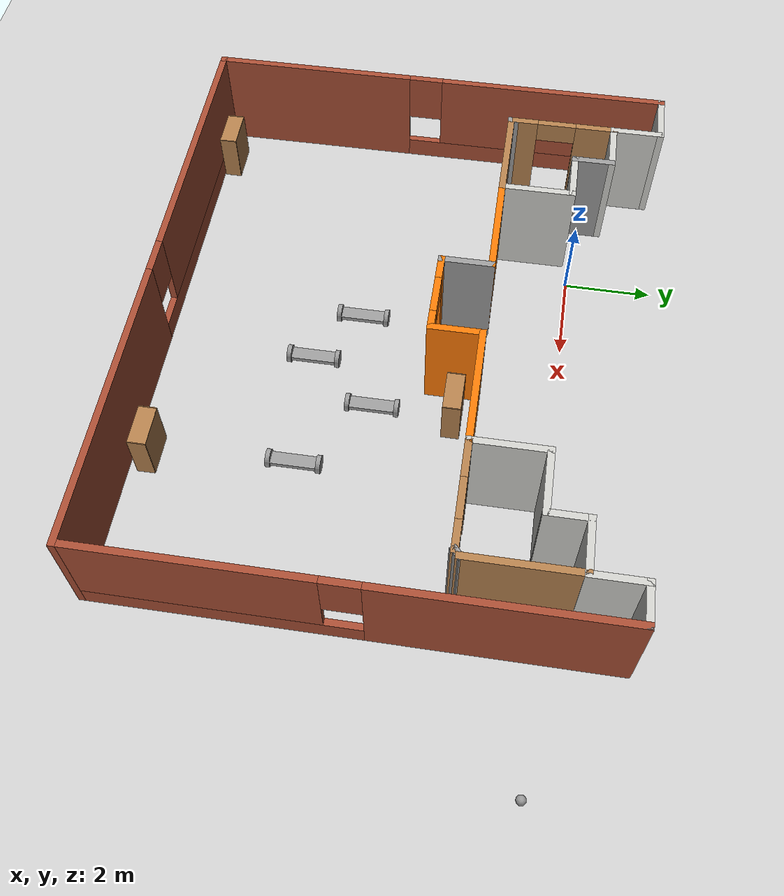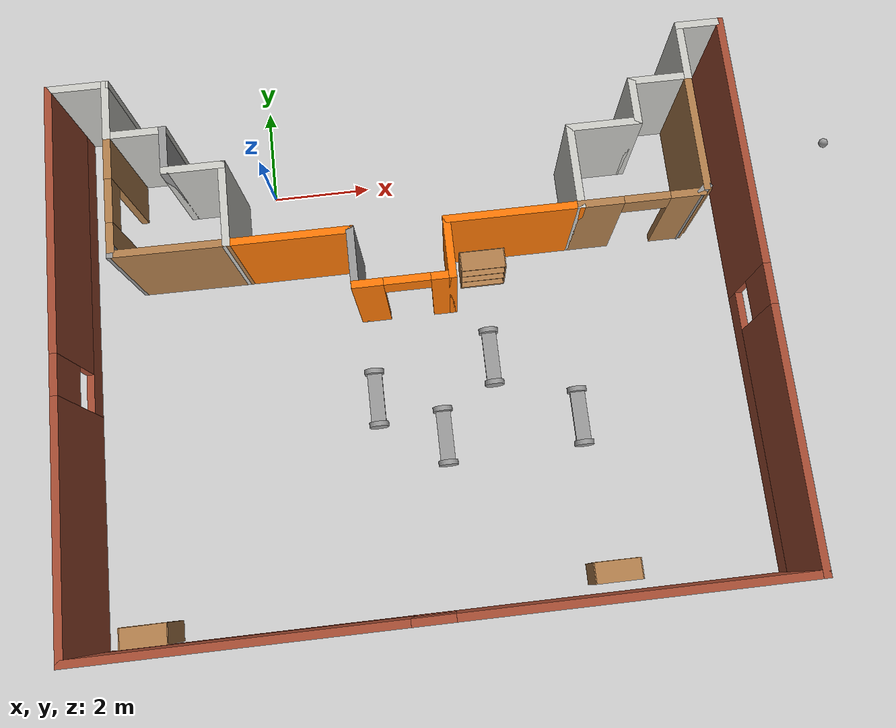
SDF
<sdf version="1.6">
 <world name="default">
  <plugin name="welcome" filename="libwelcome.so"/>
  <light name="sun" type="directional">
   <pose>0 0 10 0 -0 0</pose>
   <diffuse>0.8 0.8 0.8 1</diffuse>
   <specular>0.1 0.1 0.1 1</specular>
   <attenuation>
    <range>1000</range>
    <constant>0.9</constant>
    <linear>0.01</linear>
    <quadratic>0.001</quadratic>
   </attenuation>
   <direction>-0.5 0.5 -1</direction>
  </light>
  <model name="ground_plane">
   <static>1</static>
   <link name="link">
    <collision name="collision">
     <geometry><plane><normal>0 0 1</normal><size>100 100</size></plane></geometry>
     <surface><friction><ode><mu>100</mu><mu2>50</mu2></ode></friction></surface>
    </collision>
    <visual name="visual">
     <cast_shadows>0</cast_shadows>
     <geometry><plane><normal>0 0 1</normal><size>100 100</size></plane></geometry>
     <material>
      <script><uri>file://media/materials/scripts/gazebo.material</uri><name>Gazebo/Grey</name></script>
     </material>
    </visual>
   </link>
  </model>
  <gravity>0 0 -9.8</gravity>
  <magnetic_field>6e-06 2.3e-05 -4.2e-05</magnetic_field>
  <atmosphere type="adiabatic"/>
  <physics name="default_physics" default="0" type="ode">
   <max_step_size>0.001</max_step_size>
   <real_time_factor>1</real_time_factor>
   <real_time_update_rate>1000</real_time_update_rate>
  </physics>
  <scene><ambient>0.4 0.4 0.4 1</ambient><background>0.7 0.7 0.7 1</background><shadows>1</shadows></scene>
  <spherical_coordinates>
   <surface_model>EARTH_WGS84</surface_model>
   <latitude_deg>0</latitude_deg>
   <longitude_deg>0</longitude_deg>
   <elevation>0</elevation>
   <heading_deg>0</heading_deg>
  </spherical_coordinates>
  <model name="Building">
   <pose>2.73872 -3.65491 0 0 -0 0</pose>
   <link name="Wall_0">
    <pose>-6.7 0 0 0 -0 1.5708</pose>
    <visual name="Wall_0_Visual_0">
     <pose>-3.10618 0 1.25 0 -0 0</pose>
     <geometry><box><size>4.78763 0.15 2.5</size></box></geometry>
     <material>
      <script><uri>file://media/materials/scripts/gazebo.material</uri><name>Gazebo/Bricks</name></script>
      <ambient>1 1 1 1</ambient>
     </material>
    </visual>
    <collision name="Wall_0_Collision_0">
     <geometry><box><size>4.78763 0.15 2.5</size></box></geometry>
     <pose>-3.10618 0 1.25 0 -0 0</pose>
    </collision>
    <visual name="Wall_0_Visual_1">
     <pose>2.39382 0 0.25 0 -0 0</pose>
     <geometry><box><size>6.21237 0.15 0.5</size></box></geometry>
     <material>
      <script><uri>file://media/materials/scripts/gazebo.material</uri><name>Gazebo/Bricks</name></script>
      <ambient>1 1 1 1</ambient>
     </material>
    </visual>
    <collision name="Wall_0_Collision_1">
     <geometry><box><size>6.21237 0.15 0.5</size></box></geometry>
     <pose>2.39382 0 0.25 0 -0 0</pose>
    </collision>
    <visual name="Wall_0_Visual_2">
     <pose>2.79382 0 1.5 0 -0 0</pose>
     <geometry><box><size>5.41237 0.15 2</size></box></geometry>
     <material>
      <script><uri>file://media/materials/scripts/gazebo.material</uri><name>Gazebo/Bricks</name></script>
      <ambient>1 1 1 1</ambient>
     </material>
    </visual>
    <collision name="Wall_0_Collision_2">
     <geometry><box><size>5.41237 0.15 2</size></box></geometry>
     <pose>2.79382 0 1.5 0 -0 0</pose>
    </collision>
    <visual name="Wall_0_Visual_3">
     <pose>-0.312368 0 1.9 0 -0 0</pose>
     <geometry><box><size>0.8 0.15 1.2</size></box></geometry>
     <material>
      <script><uri>file://media/materials/scripts/gazebo.material</uri><name>Gazebo/Bricks</name></script>
      <ambient>1 1 1 1</ambient>
     </material>
    </visual>
    <collision name="Wall_0_Collision_3">
     <geometry><box><size>0.8 0.15 1.2</size></box></geometry>
     <pose>-0.312368 0 1.9 0 -0 0</pose>
    </collision>
   </link>
   <link name="Wall_1">
    <collision name="Wall_1_Collision">
     <geometry><box><size>1.26323 0.15 2.5</size></box></geometry>
     <pose>0 0 1.25 0 -0 0</pose>
    </collision>
    <visual name="Wall_1_Visual">
     <pose>0 0 1.25 0 -0 0</pose>
     <geometry><box><size>1.26323 0.15 2.5</size></box></geometry>
     <material>
      <script><uri>file://media/materials/scripts/gazebo.material</uri><name>Gazebo/CeilingTiled</name></script>
      <ambient>1 1 1 1</ambient>
     </material>
    </visual>
    <pose>-6.14339 5.425 0 0 -0 0</pose>
   </link>
   <link name="Wall_10">
    <collision name="Wall_10_Collision">
     <geometry><box><size>1.25 0.15 2.5</size></box></geometry>
     <pose>0 0 1.25 0 -0 0</pose>
    </collision>
    <visual name="Wall_10_Visual">
     <pose>0 0 1.25 0 -0 0</pose>
     <geometry><box><size>1.25 0.15 2.5</size></box></geometry>
     <material>
      <script><uri>file://media/materials/scripts/gazebo.material</uri><name>Gazebo/Grey</name></script>
      <ambient>0.996078 0.47451 0.0196078 1</ambient>
     </material>
    </visual>
    <pose>0.8 1.325 0 0 -0 1.5708</pose>
   </link>
   <link name="Wall_11">
    <collision name="Wall_11_Collision">
     <geometry><box><size>2.75 0.15 2.5</size></box></geometry>
     <pose>0 0 1.25 0 -0 0</pose>
    </collision>
    <visual name="Wall_11_Visual">
     <pose>0 0 1.25 0 -0 0</pose>
     <geometry><box><size>2.75 0.15 2.5</size></box></geometry>
     <material>
      <script><uri>file://media/materials/scripts/gazebo.material</uri><name>Gazebo/Grey</name></script>
      <ambient>0.996078 0.47451 0.0196078 1</ambient>
     </material>
    </visual>
    <pose>2.1 1.875 0 0 -0 0</pose>
   </link>
   <link name="Wall_12">
    <collision name="Wall_12_Collision">
     <geometry><box><size>1.75 0.15 2.5</size></box></geometry>
     <pose>0 0 1.25 0 -0 0</pose>
    </collision>
    <visual name="Wall_12_Visual">
     <pose>0 0 1.25 0 -0 0</pose>
     <geometry><box><size>1.75 0.15 2.5</size></box></geometry>
     <material>
      <script><uri>file://media/materials/scripts/gazebo.material</uri><name>Gazebo/CeilingTiled</name></script>
      <ambient>1 0.764706 0.305882 1</ambient>
     </material>
    </visual>
    <pose>3.4 2.675 0 0 -0 1.5708</pose>
   </link>
   <link name="Wall_13">
    <collision name="Wall_13_Collision">
     <geometry><box><size>1.5 0.15 2.5</size></box></geometry>
     <pose>0 0 1.25 0 -0 0</pose>
    </collision>
    <visual name="Wall_13_Visual">
     <pose>0 0 1.25 0 -0 0</pose>
     <geometry><box><size>1.5 0.15 2.5</size></box></geometry>
     <material>
      <script><uri>file://media/materials/scripts/gazebo.material</uri><name>Gazebo/CeilingTiled</name></script>
      <ambient>1 1 1 1</ambient>
     </material>
    </visual>
    <pose>4.075 3.475 0 0 -0 0</pose>
   </link>
   <link name="Wall_14">
    <collision name="Wall_14_Collision">
     <geometry><box><size>1 0.15 2.5</size></box></geometry>
     <pose>0 0 1.25 0 -0 0</pose>
    </collision>
    <visual name="Wall_14_Visual">
     <pose>0 0 1.25 0 -0 0</pose>
     <geometry><box><size>1 0.15 2.5</size></box></geometry>
     <material>
      <script><uri>file://media/materials/scripts/gazebo.material</uri><name>Gazebo/CeilingTiled</name></script>
      <ambient>1 1 1 1</ambient>
     </material>
    </visual>
    <pose>4.75 3.9 0 0 -0 1.5708</pose>
   </link>
   <link name="Wall_15">
    <collision name="Wall_15_Collision">
     <geometry><box><size>1.273 0.15 2.5</size></box></geometry>
     <pose>0 0 1.25 0 -0 0</pose>
    </collision>
    <visual name="Wall_15_Visual">
     <pose>0 0 1.25 0 -0 0</pose>
     <geometry><box><size>1.273 0.15 2.5</size></box></geometry>
     <material>
      <script><uri>file://media/materials/scripts/gazebo.material</uri><name>Gazebo/CeilingTiled</name></script>
      <ambient>1 1 1 1</ambient>
     </material>
    </visual>
    <pose>5.3115 4.325 0 0 -0 0</pose>
   </link>
   <link name="Wall_16">
    <collision name="Wall_16_Collision">
     <geometry><box><size>1.25 0.15 2.5</size></box></geometry>
     <pose>0 0 1.25 0 -0 0</pose>
    </collision>
    <visual name="Wall_16_Visual">
     <pose>0 0 1.25 0 -0 0</pose>
     <geometry><box><size>1.25 0.15 2.5</size></box></geometry>
     <material>
      <script><uri>file://media/materials/scripts/gazebo.material</uri><name>Gazebo/CeilingTiled</name></script>
      <ambient>1 1 1 1</ambient>
     </material>
    </visual>
    <pose>5.873 4.875 0 0 -0 1.5708</pose>
   </link>
   <link name="Wall_17">
    <collision name="Wall_17_Collision">
     <geometry><box><size>0.977 0.15 2.5</size></box></geometry>
     <pose>0 0 1.25 0 -0 0</pose>
    </collision>
    <visual name="Wall_17_Visual">
     <pose>0 0 1.25 0 -0 0</pose>
     <geometry><box><size>0.977 0.15 2.5</size></box></geometry>
     <material>
      <script><uri>file://media/materials/scripts/gazebo.material</uri><name>Gazebo/CeilingTiled</name></script>
      <ambient>1 1 1 1</ambient>
     </material>
    </visual>
    <pose>6.2865 5.425 0 0 -0 0</pose>
   </link>
   <link name="Wall_18">
    <pose>6.7 0 0 0 0 -1.5708</pose>
    <visual name="Wall_18_Visual_0">
     <pose>-2.90947 0 1.25 0 -0 0</pose>
     <geometry><box><size>5.18106 0.15 2.5</size></box></geometry>
     <material>
      <script><uri>file://media/materials/scripts/gazebo.material</uri><name>Gazebo/Bricks</name></script>
      <ambient>1 1 1 1</ambient>
     </material>
    </visual>
    <collision name="Wall_18_Collision_0">
     <geometry><box><size>5.18106 0.15 2.5</size></box></geometry>
     <pose>-2.90947 0 1.25 0 -0 0</pose>
    </collision>
    <visual name="Wall_18_Visual_1">
     <pose>2.59053 0 0.25 0 -0 0</pose>
     <geometry><box><size>5.81894 0.15 0.5</size></box></geometry>
     <material>
      <script><uri>file://media/materials/scripts/gazebo.material</uri><name>Gazebo/Bricks</name></script>
      <ambient>1 1 1 1</ambient>
     </material>
    </visual>
    <collision name="Wall_18_Collision_1">
     <geometry><box><size>5.81894 0.15 0.5</size></box></geometry>
     <pose>2.59053 0 0.25 0 -0 0</pose>
    </collision>
    <visual name="Wall_18_Visual_2">
     <pose>2.99053 0 1.5 0 -0 0</pose>
     <geometry><box><size>5.01894 0.15 2</size></box></geometry>
     <material>
      <script><uri>file://media/materials/scripts/gazebo.material</uri><name>Gazebo/Bricks</name></script>
      <ambient>1 1 1 1</ambient>
     </material>
    </visual>
    <collision name="Wall_18_Collision_2">
     <geometry><box><size>5.01894 0.15 2</size></box></geometry>
     <pose>2.99053 0 1.5 0 -0 0</pose>
    </collision>
    <visual name="Wall_18_Visual_3">
     <pose>0.081062 0 1.9 0 -0 0</pose>
     <geometry><box><size>0.8 0.15 1.2</size></box></geometry>
     <material>
      <script><uri>file://media/materials/scripts/gazebo.material</uri><name>Gazebo/Bricks</name></script>
      <ambient>1 1 1 1</ambient>
     </material>
    </visual>
    <collision name="Wall_18_Collision_3">
     <geometry><box><size>0.8 0.15 1.2</size></box></geometry>
     <pose>0.081062 0 1.9 0 -0 0</pose>
    </collision>
   </link>
   <link name="Wall_19">
    <pose>0 -5.425 0 0 -0 3.14159</pose>
    <visual name="Wall_19_Visual_0">
     <pose>-3.47411 0 1.25 0 -0 0</pose>
     <geometry><box><size>6.60178 0.15 2.5</size></box></geometry>
     <material>
      <script><uri>file://media/materials/scripts/gazebo.material</uri><name>Gazebo/Bricks</name></script>
      <ambient>1 1 1 1</ambient>
     </material>
    </visual>
    <collision name="Wall_19_Collision_0">
     <geometry><box><size>6.60178 0.15 2.5</size></box></geometry>
     <pose>-3.47411 0 1.25 0 -0 0</pose>
    </collision>
    <visual name="Wall_19_Visual_1">
     <pose>3.30089 0 0.25 0 -0 0</pose>
     <geometry><box><size>6.94822 0.15 0.5</size></box></geometry>
     <material>
      <script><uri>file://media/materials/scripts/gazebo.material</uri><name>Gazebo/Bricks</name></script>
      <ambient>1 1 1 1</ambient>
     </material>
    </visual>
    <collision name="Wall_19_Collision_1">
     <geometry><box><size>6.94822 0.15 0.5</size></box></geometry>
     <pose>3.30089 0 0.25 0 -0 0</pose>
    </collision>
    <visual name="Wall_19_Visual_2">
     <pose>3.70089 0 1.5 0 -0 0</pose>
     <geometry><box><size>6.14822 0.15 2</size></box></geometry>
     <material>
      <script><uri>file://media/materials/scripts/gazebo.material</uri><name>Gazebo/Bricks</name></script>
      <ambient>1 1 1 1</ambient>
     </material>
    </visual>
    <collision name="Wall_19_Collision_2">
     <geometry><box><size>6.14822 0.15 2</size></box></geometry>
     <pose>3.70089 0 1.5 0 -0 0</pose>
    </collision>
    <visual name="Wall_19_Visual_3">
     <pose>0.226781 0 1.9 0 -0 0</pose>
     <geometry><box><size>0.8 0.15 1.2</size></box></geometry>
     <material>
      <script><uri>file://media/materials/scripts/gazebo.material</uri><name>Gazebo/Bricks</name></script>
      <ambient>1 1 1 1</ambient>
     </material>
    </visual>
    <collision name="Wall_19_Collision_3">
     <geometry><box><size>0.8 0.15 1.2</size></box></geometry>
     <pose>0.226781 0 1.9 0 -0 0</pose>
    </collision>
   </link>
   <link name="Wall_2">
    <collision name="Wall_2_Collision">
     <geometry><box><size>1.25 0.15 2.5</size></box></geometry>
     <pose>0 0 1.25 0 -0 0</pose>
    </collision>
    <visual name="Wall_2_Visual">
     <pose>0 0 1.25 0 -0 0</pose>
     <geometry><box><size>1.25 0.15 2.5</size></box></geometry>
     <material>
      <script><uri>file://media/materials/scripts/gazebo.material</uri><name>Gazebo/CeilingTiled</name></script>
      <ambient>1 1 1 1</ambient>
     </material>
    </visual>
    <pose>-5.58678 4.875 0 0 0 -1.5708</pose>
   </link>
   <link name="Wall_25">
    <pose>-5.58678 3.16323 0 0 0 -1.5708</pose>
    <visual name="Wall_25_Visual_0">
     <pose>-0.75673 0 1.25 0 -0 0</pose>
     <geometry><box><size>0.986541 0.15 2.5</size></box></geometry>
     <material>
      <script><uri>file://media/materials/scripts/gazebo.material</uri><name>Gazebo/Wood</name></script>
      <ambient>1 1 1 1</ambient>
     </material>
    </visual>
    <collision name="Wall_25_Collision_0">
     <geometry><box><size>0.986541 0.15 2.5</size></box></geometry>
     <pose>-0.75673 0 1.25 0 -0 0</pose>
    </collision>
    <visual name="Wall_25_Visual_1">
     <pose>0.94327 0 1.25 0 -0 0</pose>
     <geometry><box><size>0.613459 0.15 2.5</size></box></geometry>
     <material>
      <script><uri>file://media/materials/scripts/gazebo.material</uri><name>Gazebo/Wood</name></script>
      <ambient>1 1 1 1</ambient>
     </material>
    </visual>
    <collision name="Wall_25_Collision_1">
     <geometry><box><size>0.613459 0.15 2.5</size></box></geometry>
     <pose>0.94327 0 1.25 0 -0 0</pose>
    </collision>
    <visual name="Wall_25_Visual_2">
     <pose>0.186541 0 2.25 0 -0 0</pose>
     <geometry><box><size>0.9 0.15 0.5</size></box></geometry>
     <material>
      <script><uri>file://media/materials/scripts/gazebo.material</uri><name>Gazebo/Wood</name></script>
      <ambient>1 1 1 1</ambient>
     </material>
    </visual>
    <collision name="Wall_25_Collision_2">
     <geometry><box><size>0.9 0.15 0.5</size></box></geometry>
     <pose>0.186541 0 2.25 0 -0 0</pose>
    </collision>
   </link>
   <link name="Wall_27">
    <collision name="Wall_27_Collision">
     <geometry><box><size>0.25 0.15 2.5</size></box></geometry>
     <pose>0 0 1.25 0 -0 0</pose>
    </collision>
    <visual name="Wall_27_Visual">
     <pose>0 0 1.25 0 -0 0</pose>
     <geometry><box><size>0.25 0.15 2.5</size></box></geometry>
     <material>
      <script><uri>file://media/materials/scripts/gazebo.material</uri><name>Gazebo/Grey</name></script>
      <ambient>1 1 1 1</ambient>
     </material>
    </visual>
    <pose>-5.58678 1.93823 0 0 0 -1.5708</pose>
   </link>
   <link name="Wall_28">
    <collision name="Wall_28_Collision">
     <geometry><box><size>2.33682 0.15 2.5</size></box></geometry>
     <pose>0 0 1.25 0 -0 0</pose>
    </collision>
    <visual name="Wall_28_Visual">
     <pose>0 0 1.25 0 -0 0</pose>
     <geometry><box><size>2.33682 0.15 2.5</size></box></geometry>
     <material>
      <script><uri>file://media/materials/scripts/gazebo.material</uri><name>Gazebo/Wood</name></script>
      <ambient>1 1 1 1</ambient>
     </material>
    </visual>
    <pose>-4.49339 1.88161 0 0 0 -0.006048</pose>
   </link>
   <link name="Wall_3">
    <collision name="Wall_3_Collision">
     <geometry><box><size>1.2371 0.15 2.5</size></box></geometry>
     <pose>0 0 1.25 0 -0 0</pose>
    </collision>
    <visual name="Wall_3_Visual">
     <pose>0 0 1.25 0 -0 0</pose>
     <geometry><box><size>1.2371 0.15 2.5</size></box></geometry>
     <material>
      <script><uri>file://media/materials/scripts/gazebo.material</uri><name>Gazebo/CeilingTiled</name></script>
      <ambient>1 1 1 1</ambient>
     </material>
    </visual>
    <pose>-5.04339 4.325 0 0 -0 0</pose>
   </link>
   <link name="Wall_31">
    <collision name="Wall_31_Collision">
     <geometry><box><size>2.5 0.15 2.5</size></box></geometry>
     <pose>0 0 1.25 0 -0 0</pose>
    </collision>
    <visual name="Wall_31_Visual">
     <pose>0 0 1.25 0 -0 0</pose>
     <geometry><box><size>2.5 0.15 2.5</size></box></geometry>
     <material>
      <script><uri>file://media/materials/scripts/gazebo.material</uri><name>Gazebo/Wood</name></script>
      <ambient>1 1 1 1</ambient>
     </material>
    </visual>
    <pose>5.8615 3.15 0 0 -0 1.5708</pose>
   </link>
   <link name="Wall_33">
    <pose>4.575 1.875 0 0 -0 0</pose>
    <visual name="Wall_33_Visual_0">
     <pose>-0.797379 0 1.25 0 -0 0</pose>
     <geometry><box><size>0.905241 0.15 2.5</size></box></geometry>
     <material>
      <script><uri>file://media/materials/scripts/gazebo.material</uri><name>Gazebo/Wood</name></script>
      <ambient>1 1 1 1</ambient>
     </material>
    </visual>
    <collision name="Wall_33_Collision_0">
     <geometry><box><size>0.905241 0.15 2.5</size></box></geometry>
     <pose>-0.797379 0 1.25 0 -0 0</pose>
    </collision>
    <visual name="Wall_33_Visual_1">
     <pose>0.902621 0 1.25 0 -0 0</pose>
     <geometry><box><size>0.694759 0.15 2.5</size></box></geometry>
     <material>
      <script><uri>file://media/materials/scripts/gazebo.material</uri><name>Gazebo/Wood</name></script>
      <ambient>1 1 1 1</ambient>
     </material>
    </visual>
    <collision name="Wall_33_Collision_1">
     <geometry><box><size>0.694759 0.15 2.5</size></box></geometry>
     <pose>0.902621 0 1.25 0 -0 0</pose>
    </collision>
    <visual name="Wall_33_Visual_2">
     <pose>0.105241 0 2.25 0 -0 0</pose>
     <geometry><box><size>0.9 0.15 0.5</size></box></geometry>
     <material>
      <script><uri>file://media/materials/scripts/gazebo.material</uri><name>Gazebo/Wood</name></script>
      <ambient>1 1 1 1</ambient>
     </material>
    </visual>
    <collision name="Wall_33_Collision_2">
     <geometry><box><size>0.9 0.15 0.5</size></box></geometry>
     <pose>0.105241 0 2.25 0 -0 0</pose>
    </collision>
   </link>
   <link name="Wall_36">
    <collision name="Wall_36_Collision">
     <geometry><box><size>0.299774 0.15 2.5</size></box></geometry>
     <pose>0 0 1.25 0 -0 0</pose>
    </collision>
    <visual name="Wall_36_Visual">
     <pose>0 0 1.25 0 -0 0</pose>
     <geometry><box><size>0.299774 0.15 2.5</size></box></geometry>
     <material>
      <script><uri>file://media/materials/scripts/gazebo.material</uri><name>Gazebo/Grey</name></script>
      <ambient>1 1 1 1</ambient>
     </material>
    </visual>
    <pose>5.80575 1.925 0 0 0 -2.41052</pose>
   </link>
   <link name="Wall_4">
    <collision name="Wall_4_Collision">
     <geometry><box><size>1 0.15 2.5</size></box></geometry>
     <pose>0 0 1.25 0 -0 0</pose>
    </collision>
    <visual name="Wall_4_Visual">
     <pose>0 0 1.25 0 -0 0</pose>
     <geometry><box><size>1 0.15 2.5</size></box></geometry>
     <material>
      <script><uri>file://media/materials/scripts/gazebo.material</uri><name>Gazebo/Grey</name></script>
      <ambient>1 1 1 1</ambient>
     </material>
    </visual>
    <pose>-4.5 3.9 0 0 0 -1.5708</pose>
   </link>
   <link name="Wall_5">
    <collision name="Wall_5_Collision">
     <geometry><box><size>1.23677 0.15 2.5</size></box></geometry>
     <pose>0 0 1.25 0 -0 0</pose>
    </collision>
    <visual name="Wall_5_Visual">
     <pose>0 0 1.25 0 -0 0</pose>
     <geometry><box><size>1.23677 0.15 2.5</size></box></geometry>
     <material>
      <script><uri>file://media/materials/scripts/gazebo.material</uri><name>Gazebo/CeilingTiled</name></script>
      <ambient>1 1 1 1</ambient>
     </material>
    </visual>
    <pose>-3.95661 3.475 0 0 -0 0</pose>
   </link>
   <link name="Wall_6">
    <collision name="Wall_6_Collision">
     <geometry><box><size>1.75 0.15 2.5</size></box></geometry>
     <pose>0 0 1.25 0 -0 0</pose>
    </collision>
    <visual name="Wall_6_Visual">
     <pose>0 0 1.25 0 -0 0</pose>
     <geometry><box><size>1.75 0.15 2.5</size></box></geometry>
     <material>
      <script><uri>file://media/materials/scripts/gazebo.material</uri><name>Gazebo/CeilingTiled</name></script>
      <ambient>1 0.764706 0.305882 1</ambient>
     </material>
    </visual>
    <pose>-3.4 2.675 0 0 0 -1.5708</pose>
   </link>
   <link name="Wall_7">
    <collision name="Wall_7_Collision">
     <geometry><box><size>2.5 0.15 2.5</size></box></geometry>
     <pose>0 0 1.25 0 -0 0</pose>
    </collision>
    <visual name="Wall_7_Visual">
     <pose>0 0 1.25 0 -0 0</pose>
     <geometry><box><size>2.5 0.15 2.5</size></box></geometry>
     <material>
      <script><uri>file://media/materials/scripts/gazebo.material</uri><name>Gazebo/Grey</name></script>
      <ambient>0.996078 0.47451 0.0196078 1</ambient>
     </material>
    </visual>
    <pose>-2.225 1.875 0 0 -0 0</pose>
   </link>
   <link name="Wall_8">
    <collision name="Wall_8_Collision">
     <geometry><box><size>1.25 0.15 2.5</size></box></geometry>
     <pose>0 0 1.25 0 -0 0</pose>
    </collision>
    <visual name="Wall_8_Visual">
     <pose>0 0 1.25 0 -0 0</pose>
     <geometry><box><size>1.25 0.15 2.5</size></box></geometry>
     <material>
      <script><uri>file://media/materials/scripts/gazebo.material</uri><name>Gazebo/Grey</name></script>
      <ambient>1 1 1 1</ambient>
     </material>
    </visual>
    <pose>-1.05 1.325 0 0 0 -1.5708</pose>
   </link>
   <link name="Wall_9">
    <pose>-0.125 0.775 0 0 -0 0</pose>
    <visual name="Wall_9_Visual_0">
     <pose>-0.694934 0 1.25 0 -0 0</pose>
     <geometry><box><size>0.610133 0.15 2.5</size></box></geometry>
     <material>
      <script><uri>file://media/materials/scripts/gazebo.material</uri><name>Gazebo/Grey</name></script>
      <ambient>0.996078 0.47451 0.0196078 1</ambient>
     </material>
    </visual>
    <collision name="Wall_9_Collision_0">
     <geometry><box><size>0.610133 0.15 2.5</size></box></geometry>
     <pose>-0.694934 0 1.25 0 -0 0</pose>
    </collision>
    <visual name="Wall_9_Visual_1">
     <pose>0.755066 0 1.25 0 -0 0</pose>
     <geometry><box><size>0.489867 0.15 2.5</size></box></geometry>
     <material>
      <script><uri>file://media/materials/scripts/gazebo.material</uri><name>Gazebo/Grey</name></script>
      <ambient>0.996078 0.47451 0.0196078 1</ambient>
     </material>
    </visual>
    <collision name="Wall_9_Collision_1">
     <geometry><box><size>0.489867 0.15 2.5</size></box></geometry>
     <pose>0.755066 0 1.25 0 -0 0</pose>
    </collision>
    <visual name="Wall_9_Visual_2">
     <pose>0.060133 0 2.25 0 -0 0</pose>
     <geometry><box><size>0.9 0.15 0.5</size></box></geometry>
     <material>
      <script><uri>file://media/materials/scripts/gazebo.material</uri><name>Gazebo/Grey</name></script>
      <ambient>0.996078 0.47451 0.0196078 1</ambient>
     </material>
    </visual>
    <collision name="Wall_9_Collision_2">
     <geometry><box><size>0.9 0.15 0.5</size></box></geometry>
     <pose>0.060133 0 2.25 0 -0 0</pose>
    </collision>
   </link>
   <static>1</static>
  </model>
  <model name="2wlrobot">
   <link name="link_1">
    <pose>-3e-06 2e-06 0 0 -0 0</pose>
    <inertial>
     <mass>1</mass>
     <inertia>
      <ixx>0.166667</ixx>
      <ixy>0</ixy>
      <ixz>0</ixz>
      <iyy>0.166667</iyy>
      <iyz>0</iyz>
      <izz>0.166667</izz>
     </inertia>
    </inertial>
    <visual name="visual">
     <geometry><box><size>0.3 1 0.1</size></box></geometry>
     <material>
      <lighting>1</lighting>
      <script><uri>file://media/materials/scripts/gazebo.material</uri><name>Gazebo/Grey</name></script>
      <ambient>0.3 0.3 0.3 1</ambient>
      <diffuse>0.7 0.7 0.7 1</diffuse>
      <specular>0.01 0.01 0.01 1</specular>
      <emissive>0 0 0 1</emissive>
      <shader type="vertex"><normal_map>__default__</normal_map></shader>
     </material>
    </visual>
    <collision name="collision">
     <geometry><box><size>0.3 1 0.1</size></box></geometry>
     <surface>
      <friction>
       <ode><mu>1</mu><mu2>1</mu2><fdir1>0 0 0</fdir1><slip1>0</slip1><slip2>0</slip2></ode>
       <torsional>
        <coefficient>1</coefficient>
        <patch_radius>0</patch_radius>
        <surface_radius>0</surface_radius>
        <use_patch_radius>1</use_patch_radius>
        <ode><slip>0</slip></ode>
       </torsional>
      </friction>
      <bounce><restitution_coefficient>0</restitution_coefficient><threshold>1e+06</threshold></bounce>
      <contact>
       <collide_without_contact>0</collide_without_contact>
       <collide_without_contact_bitmask>1</collide_without_contact_bitmask>
       <collide_bitmask>1</collide_bitmask>
       <ode>
        <soft_cfm>0</soft_cfm>
        <soft_erp>0.2</soft_erp>
        <kp>1e+13</kp>
        <kd>1</kd>
        <max_vel>0.01</max_vel>
        <min_depth>0</min_depth>
       </ode>
       <bullet>
        <split_impulse>1</split_impulse>
        <split_impulse_penetration_threshold>-0.01</split_impulse_penetration_threshold>
        <soft_cfm>0</soft_cfm>
        <soft_erp>0.2</soft_erp>
        <kp>1e+13</kp>
        <kd>1</kd>
       </bullet>
      </contact>
     </surface>
    </collision>
   </link>
   <link name="link_2">
    <pose>-3e-06 -0.550157 0 1.57 -0 0</pose>
    <inertial>
     <mass>1</mass>
     <inertia><ixx>0.145833</ixx><ixy>0</ixy><ixz>0</ixz><iyy>0.145833</iyy><iyz>0</iyz><izz>0.125</izz></inertia>
     <pose>0 0 0.2 1.57 -0 0</pose>
    </inertial>
    <visual name="visual">
     <geometry><cylinder><radius>0.2</radius><length>0.1</length></cylinder></geometry>
     <material>
      <lighting>1</lighting>
      <script><uri>file://media/materials/scripts/gazebo.material</uri><name>Gazebo/Grey</name></script>
      <ambient>0.3 0.3 0.3 1</ambient>
      <diffuse>0.7 0.7 0.7 1</diffuse>
      <specular>0.01 0.01 0.01 1</specular>
      <emissive>0 0 0 1</emissive>
      <shader type="vertex"><normal_map>__default__</normal_map></shader>
     </material>
    </visual>
    <collision name="collision">
     <geometry><cylinder><radius>0.2</radius><length>0.1</length></cylinder></geometry>
     <surface>
      <friction>
       <ode><mu>1</mu><mu2>1</mu2><fdir1>0 0 0</fdir1><slip1>0</slip1><slip2>0</slip2></ode>
       <torsional>
        <coefficient>1</coefficient>
        <patch_radius>0</patch_radius>
        <surface_radius>0</surface_radius>
        <use_patch_radius>1</use_patch_radius>
        <ode><slip>0</slip></ode>
       </torsional>
      </friction>
      <bounce><restitution_coefficient>0</restitution_coefficient><threshold>1e+06</threshold></bounce>
      <contact>
       <collide_without_contact>0</collide_without_contact>
       <collide_without_contact_bitmask>1</collide_without_contact_bitmask>
       <collide_bitmask>1</collide_bitmask>
       <ode>
        <soft_cfm>0</soft_cfm>
        <soft_erp>0.2</soft_erp>
        <kp>1e+13</kp>
        <kd>1</kd>
        <max_vel>0.01</max_vel>
        <min_depth>0</min_depth>
       </ode>
       <bullet>
        <split_impulse>1</split_impulse>
        <split_impulse_penetration_threshold>-0.01</split_impulse_penetration_threshold>
        <soft_cfm>0</soft_cfm>
        <soft_erp>0.2</soft_erp>
        <kp>1e+13</kp>
        <kd>1</kd>
       </bullet>
      </contact>
     </surface>
    </collision>
   </link>
   <link name="link_2_clone">
    <pose>-3e-06 0.550162 0 1.57 -0 0</pose>
    <inertial>
     <mass>1</mass>
     <inertia><ixx>0.145833</ixx><ixy>0</ixy><ixz>0</ixz><iyy>0.145833</iyy><iyz>0</iyz><izz>0.125</izz></inertia>
     <pose>0 0 0.2 1.57 -0 0</pose>
    </inertial>
    <visual name="visual">
     <geometry><cylinder><radius>0.2</radius><length>0.1</length></cylinder></geometry>
     <material>
      <lighting>1</lighting>
      <script><uri>file://media/materials/scripts/gazebo.material</uri><name>Gazebo/Grey</name></script>
      <ambient>0.3 0.3 0.3 1</ambient>
      <diffuse>0.7 0.7 0.7 1</diffuse>
      <specular>0.01 0.01 0.01 1</specular>
      <emissive>0 0 0 1</emissive>
      <shader type="vertex"><normal_map>__default__</normal_map></shader>
     </material>
    </visual>
    <collision name="collision">
     <geometry><cylinder><radius>0.2</radius><length>0.1</length></cylinder></geometry>
     <surface>
      <friction>
       <ode><mu>1</mu><mu2>1</mu2><fdir1>0 0 0</fdir1><slip1>0</slip1><slip2>0</slip2></ode>
       <torsional>
        <coefficient>1</coefficient>
        <patch_radius>0</patch_radius>
        <surface_radius>0</surface_radius>
        <use_patch_radius>1</use_patch_radius>
        <ode><slip>0</slip></ode>
       </torsional>
      </friction>
      <bounce><restitution_coefficient>0</restitution_coefficient><threshold>1e+06</threshold></bounce>
      <contact>
       <collide_without_contact>0</collide_without_contact>
       <collide_without_contact_bitmask>1</collide_without_contact_bitmask>
       <collide_bitmask>1</collide_bitmask>
       <ode>
        <soft_cfm>0</soft_cfm>
        <soft_erp>0.2</soft_erp>
        <kp>1e+13</kp>
        <kd>1</kd>
        <max_vel>0.01</max_vel>
        <min_depth>0</min_depth>
       </ode>
       <bullet>
        <split_impulse>1</split_impulse>
        <split_impulse_penetration_threshold>-0.01</split_impulse_penetration_threshold>
        <soft_cfm>0</soft_cfm>
        <soft_erp>0.2</soft_erp>
        <kp>1e+13</kp>
        <kd>1</kd>
       </bullet>
      </contact>
     </surface>
    </collision>
   </link>
   <joint name="link_1_JOINT_0" type="revolute">
    <parent>link_1</parent>
    <child>link_2</child>
    <axis>
     <xyz>0 0 1</xyz>
     <use_parent_model_frame>0</use_parent_model_frame>
     <limit>
      <lower>-1.79769e+308</lower>
      <upper>1.79769e+308</upper>
      <effort>-1</effort>
      <velocity>-1</velocity>
     </limit>
     <dynamics>
      <spring_reference>0</spring_reference>
      <spring_stiffness>0</spring_stiffness>
      <damping>0</damping>
     </dynamics>
    </axis>
    <physics>
     <ode><limit><cfm>0</cfm><erp>0.2</erp></limit><suspension><cfm>0</cfm><erp>0.2</erp></suspension></ode>
    </physics>
   </joint>
   <joint name="link_1_JOINT_1" type="revolute">
    <parent>link_1</parent>
    <child>link_2_clone</child>
    <axis>
     <xyz>0 0 1</xyz>
     <use_parent_model_frame>0</use_parent_model_frame>
     <limit>
      <lower>-1.79769e+308</lower>
      <upper>1.79769e+308</upper>
      <effort>-1</effort>
      <velocity>-1</velocity>
     </limit>
     <dynamics>
      <spring_reference>0</spring_reference>
      <spring_stiffness>0</spring_stiffness>
      <damping>0</damping>
     </dynamics>
    </axis>
    <physics>
     <ode><limit><cfm>0</cfm><erp>0.2</erp></limit><suspension><cfm>0</cfm><erp>0.2</erp></suspension></ode>
    </physics>
   </joint>
   <static>0</static>
   <pose>5.85656 -5.48243 0.200037 4e-06 -0 0</pose>
  </model>
  <model name="2wlrobot_clone">
   <link name="link_1">
    <pose>-3e-06 2e-06 0 0 -0 0</pose>
    <inertial>
     <mass>1</mass>
     <inertia>
      <ixx>0.166667</ixx>
      <ixy>0</ixy>
      <ixz>0</ixz>
      <iyy>0.166667</iyy>
      <iyz>0</iyz>
      <izz>0.166667</izz>
     </inertia>
    </inertial>
    <visual name="visual">
     <geometry><box><size>0.3 1 0.1</size></box></geometry>
     <material>
      <lighting>1</lighting>
      <script><uri>file://media/materials/scripts/gazebo.material</uri><name>Gazebo/Grey</name></script>
      <ambient>0.3 0.3 0.3 1</ambient>
      <diffuse>0.7 0.7 0.7 1</diffuse>
      <specular>0.01 0.01 0.01 1</specular>
      <emissive>0 0 0 1</emissive>
      <shader type="vertex"><normal_map>__default__</normal_map></shader>
     </material>
    </visual>
    <collision name="collision">
     <geometry><box><size>0.3 1 0.1</size></box></geometry>
     <surface>
      <friction>
       <ode><mu>1</mu><mu2>1</mu2><fdir1>0 0 0</fdir1><slip1>0</slip1><slip2>0</slip2></ode>
       <torsional>
        <coefficient>1</coefficient>
        <patch_radius>0</patch_radius>
        <surface_radius>0</surface_radius>
        <use_patch_radius>1</use_patch_radius>
        <ode><slip>0</slip></ode>
       </torsional>
      </friction>
      <bounce><restitution_coefficient>0</restitution_coefficient><threshold>1e+06</threshold></bounce>
      <contact>
       <collide_without_contact>0</collide_without_contact>
       <collide_without_contact_bitmask>1</collide_without_contact_bitmask>
       <collide_bitmask>1</collide_bitmask>
       <ode>
        <soft_cfm>0</soft_cfm>
        <soft_erp>0.2</soft_erp>
        <kp>1e+13</kp>
        <kd>1</kd>
        <max_vel>0.01</max_vel>
        <min_depth>0</min_depth>
       </ode>
       <bullet>
        <split_impulse>1</split_impulse>
        <split_impulse_penetration_threshold>-0.01</split_impulse_penetration_threshold>
        <soft_cfm>0</soft_cfm>
        <soft_erp>0.2</soft_erp>
        <kp>1e+13</kp>
        <kd>1</kd>
       </bullet>
      </contact>
     </surface>
    </collision>
   </link>
   <link name="link_2">
    <pose>-3e-06 -0.550157 0 1.57 -0 0</pose>
    <inertial>
     <mass>1</mass>
     <inertia><ixx>0.145833</ixx><ixy>0</ixy><ixz>0</ixz><iyy>0.145833</iyy><iyz>0</iyz><izz>0.125</izz></inertia>
     <pose>0 0 0.2 1.57 -0 0</pose>
    </inertial>
    <visual name="visual">
     <geometry><cylinder><radius>0.2</radius><length>0.1</length></cylinder></geometry>
     <material>
      <lighting>1</lighting>
      <script><uri>file://media/materials/scripts/gazebo.material</uri><name>Gazebo/Grey</name></script>
      <ambient>0.3 0.3 0.3 1</ambient>
      <diffuse>0.7 0.7 0.7 1</diffuse>
      <specular>0.01 0.01 0.01 1</specular>
      <emissive>0 0 0 1</emissive>
      <shader type="vertex"><normal_map>__default__</normal_map></shader>
     </material>
    </visual>
    <collision name="collision">
     <geometry><cylinder><radius>0.2</radius><length>0.1</length></cylinder></geometry>
     <surface>
      <friction>
       <ode><mu>1</mu><mu2>1</mu2><fdir1>0 0 0</fdir1><slip1>0</slip1><slip2>0</slip2></ode>
       <torsional>
        <coefficient>1</coefficient>
        <patch_radius>0</patch_radius>
        <surface_radius>0</surface_radius>
        <use_patch_radius>1</use_patch_radius>
        <ode><slip>0</slip></ode>
       </torsional>
      </friction>
      <bounce><restitution_coefficient>0</restitution_coefficient><threshold>1e+06</threshold></bounce>
      <contact>
       <collide_without_contact>0</collide_without_contact>
       <collide_without_contact_bitmask>1</collide_without_contact_bitmask>
       <collide_bitmask>1</collide_bitmask>
       <ode>
        <soft_cfm>0</soft_cfm>
        <soft_erp>0.2</soft_erp>
        <kp>1e+13</kp>
        <kd>1</kd>
        <max_vel>0.01</max_vel>
        <min_depth>0</min_depth>
       </ode>
       <bullet>
        <split_impulse>1</split_impulse>
        <split_impulse_penetration_threshold>-0.01</split_impulse_penetration_threshold>
        <soft_cfm>0</soft_cfm>
        <soft_erp>0.2</soft_erp>
        <kp>1e+13</kp>
        <kd>1</kd>
       </bullet>
      </contact>
     </surface>
    </collision>
   </link>
   <link name="link_2_clone">
    <pose>-3e-06 0.550162 0 1.57 -0 0</pose>
    <inertial>
     <mass>1</mass>
     <inertia><ixx>0.145833</ixx><ixy>0</ixy><ixz>0</ixz><iyy>0.145833</iyy><iyz>0</iyz><izz>0.125</izz></inertia>
     <pose>0 0 0.2 1.57 -0 0</pose>
    </inertial>
    <visual name="visual">
     <geometry><cylinder><radius>0.2</radius><length>0.1</length></cylinder></geometry>
     <material>
      <lighting>1</lighting>
      <script><uri>file://media/materials/scripts/gazebo.material</uri><name>Gazebo/Grey</name></script>
      <ambient>0.3 0.3 0.3 1</ambient>
      <diffuse>0.7 0.7 0.7 1</diffuse>
      <specular>0.01 0.01 0.01 1</specular>
      <emissive>0 0 0 1</emissive>
      <shader type="vertex"><normal_map>__default__</normal_map></shader>
     </material>
    </visual>
    <collision name="collision">
     <geometry><cylinder><radius>0.2</radius><length>0.1</length></cylinder></geometry>
     <surface>
      <friction>
       <ode><mu>1</mu><mu2>1</mu2><fdir1>0 0 0</fdir1><slip1>0</slip1><slip2>0</slip2></ode>
       <torsional>
        <coefficient>1</coefficient>
        <patch_radius>0</patch_radius>
        <surface_radius>0</surface_radius>
        <use_patch_radius>1</use_patch_radius>
        <ode><slip>0</slip></ode>
       </torsional>
      </friction>
      <bounce><restitution_coefficient>0</restitution_coefficient><threshold>1e+06</threshold></bounce>
      <contact>
       <collide_without_contact>0</collide_without_contact>
       <collide_without_contact_bitmask>1</collide_without_contact_bitmask>
       <collide_bitmask>1</collide_bitmask>
       <ode>
        <soft_cfm>0</soft_cfm>
        <soft_erp>0.2</soft_erp>
        <kp>1e+13</kp>
        <kd>1</kd>
        <max_vel>0.01</max_vel>
        <min_depth>0</min_depth>
       </ode>
       <bullet>
        <split_impulse>1</split_impulse>
        <split_impulse_penetration_threshold>-0.01</split_impulse_penetration_threshold>
        <soft_cfm>0</soft_cfm>
        <soft_erp>0.2</soft_erp>
        <kp>1e+13</kp>
        <kd>1</kd>
       </bullet>
      </contact>
     </surface>
    </collision>
   </link>
   <joint name="link_1_JOINT_0" type="revolute">
    <parent>link_1</parent>
    <child>link_2</child>
    <axis>
     <xyz>0 0 1</xyz>
     <use_parent_model_frame>0</use_parent_model_frame>
     <limit>
      <lower>-1.79769e+308</lower>
      <upper>1.79769e+308</upper>
      <effort>-1</effort>
      <velocity>-1</velocity>
     </limit>
     <dynamics>
      <spring_reference>0</spring_reference>
      <spring_stiffness>0</spring_stiffness>
      <damping>0</damping>
     </dynamics>
    </axis>
    <physics>
     <ode><limit><cfm>0</cfm><erp>0.2</erp></limit><suspension><cfm>0</cfm><erp>0.2</erp></suspension></ode>
    </physics>
   </joint>
   <joint name="link_1_JOINT_1" type="revolute">
    <parent>link_1</parent>
    <child>link_2_clone</child>
    <axis>
     <xyz>0 0 1</xyz>
     <use_parent_model_frame>0</use_parent_model_frame>
     <limit>
      <lower>-1.79769e+308</lower>
      <upper>1.79769e+308</upper>
      <effort>-1</effort>
      <velocity>-1</velocity>
     </limit>
     <dynamics>
      <spring_reference>0</spring_reference>
      <spring_stiffness>0</spring_stiffness>
      <damping>0</damping>
     </dynamics>
    </axis>
    <physics>
     <ode><limit><cfm>0</cfm><erp>0.2</erp></limit><suspension><cfm>0</cfm><erp>0.2</erp></suspension></ode>
    </physics>
   </joint>
   <static>0</static>
   <pose>3.0758 -5.57549 0.200037 4e-06 -0 0</pose>
  </model>
  <model name="bookshelf">
   <static>1</static>
   <link name="link">
    <inertial><mass>1</mass></inertial>
    <collision name="back">
     <pose>0 0.005 0.6 0 -0 0</pose>
     <geometry><box><size>0.9 0.01 1.2</size></box></geometry>
    </collision>
    <visual name="visual1">
     <pose>0 0.005 0.6 0 -0 0</pose>
     <geometry><box><size>0.9 0.01 1.2</size></box></geometry>
     <material>
      <script><uri>file://media/materials/scripts/gazebo.material</uri><name>Gazebo/Wood</name></script>
     </material>
    </visual>
    <collision name="left_side">
     <pose>0.45 -0.195 0.6 0 -0 0</pose>
     <geometry><box><size>0.02 0.4 1.2</size></box></geometry>
    </collision>
    <visual name="visual2">
     <pose>0.45 -0.195 0.6 0 -0 0</pose>
     <geometry><box><size>0.02 0.4 1.2</size></box></geometry>
     <material>
      <script><uri>file://media/materials/scripts/gazebo.material</uri><name>Gazebo/Wood</name></script>
     </material>
    </visual>
    <collision name="right_side">
     <pose>-0.45 -0.195 0.6 0 -0 0</pose>
     <geometry><box><size>0.02 0.4 1.2</size></box></geometry>
    </collision>
    <visual name="visual3">
     <pose>-0.45 -0.195 0.6 0 -0 0</pose>
     <geometry><box><size>0.02 0.4 1.2</size></box></geometry>
     <material>
      <script><uri>file://media/materials/scripts/gazebo.material</uri><name>Gazebo/Wood</name></script>
     </material>
    </visual>
    <collision name="bottom">
     <pose>0 -0.195 0.03 0 -0 0</pose>
     <geometry><box><size>0.88 0.4 0.06</size></box></geometry>
    </collision>
    <visual name="visual4">
     <pose>0 -0.195 0.03 0 -0 0</pose>
     <geometry><box><size>0.88 0.4 0.06</size></box></geometry>
     <material>
      <script><uri>file://media/materials/scripts/gazebo.material</uri><name>Gazebo/Wood</name></script>
     </material>
    </visual>
    <collision name="top">
     <pose>0 -0.195 1.19 0 -0 0</pose>
     <geometry><box><size>0.88 0.4 0.02</size></box></geometry>
    </collision>
    <visual name="visual5">
     <pose>0 -0.195 1.19 0 -0 0</pose>
     <geometry><box><size>0.88 0.4 0.02</size></box></geometry>
     <material>
      <script><uri>file://media/materials/scripts/gazebo.material</uri><name>Gazebo/Wood</name></script>
     </material>
    </visual>
    <collision name="low_shelf">
     <pose>0 -0.195 0.43 0 -0 0</pose>
     <geometry><box><size>0.88 0.4 0.02</size></box></geometry>
    </collision>
    <visual name="visual6">
     <pose>0 -0.195 0.43 0 -0 0</pose>
     <geometry><box><size>0.88 0.4 0.02</size></box></geometry>
     <material>
      <script><uri>file://media/materials/scripts/gazebo.material</uri><name>Gazebo/Wood</name></script>
     </material>
    </visual>
    <collision name="high_shelf">
     <pose>0 -0.195 0.8 0 -0 0</pose>
     <geometry><box><size>0.88 0.4 0.02</size></box></geometry>
    </collision>
    <visual name="visual7">
     <pose>0 -0.195 0.8 0 -0 0</pose>
     <geometry><box><size>0.88 0.4 0.02</size></box></geometry>
     <material>
      <script><uri>file://media/materials/scripts/gazebo.material</uri><name>Gazebo/Wood</name></script>
     </material>
    </visual>
   </link>
   <pose>6.0195 -8.41915 0 0 -0 0</pose>
  </model>
  <model name="bookshelf_clone">
   <static>1</static>
   <link name="link">
    <inertial><mass>1</mass></inertial>
    <collision name="back">
     <pose>0 0.005 0.6 0 -0 0</pose>
     <geometry><box><size>0.9 0.01 1.2</size></box></geometry>
    </collision>
    <visual name="visual1">
     <pose>0 0.005 0.6 0 -0 0</pose>
     <geometry><box><size>0.9 0.01 1.2</size></box></geometry>
     <material>
      <script><uri>file://media/materials/scripts/gazebo.material</uri><name>Gazebo/Wood</name></script>
     </material>
    </visual>
    <collision name="left_side">
     <pose>0.45 -0.195 0.6 0 -0 0</pose>
     <geometry><box><size>0.02 0.4 1.2</size></box></geometry>
    </collision>
    <visual name="visual2">
     <pose>0.45 -0.195 0.6 0 -0 0</pose>
     <geometry><box><size>0.02 0.4 1.2</size></box></geometry>
     <material>
      <script><uri>file://media/materials/scripts/gazebo.material</uri><name>Gazebo/Wood</name></script>
     </material>
    </visual>
    <collision name="right_side">
     <pose>-0.45 -0.195 0.6 0 -0 0</pose>
     <geometry><box><size>0.02 0.4 1.2</size></box></geometry>
    </collision>
    <visual name="visual3">
     <pose>-0.45 -0.195 0.6 0 -0 0</pose>
     <geometry><box><size>0.02 0.4 1.2</size></box></geometry>
     <material>
      <script><uri>file://media/materials/scripts/gazebo.material</uri><name>Gazebo/Wood</name></script>
     </material>
    </visual>
    <collision name="bottom">
     <pose>0 -0.195 0.03 0 -0 0</pose>
     <geometry><box><size>0.88 0.4 0.06</size></box></geometry>
    </collision>
    <visual name="visual4">
     <pose>0 -0.195 0.03 0 -0 0</pose>
     <geometry><box><size>0.88 0.4 0.06</size></box></geometry>
     <material>
      <script><uri>file://media/materials/scripts/gazebo.material</uri><name>Gazebo/Wood</name></script>
     </material>
    </visual>
    <collision name="top">
     <pose>0 -0.195 1.19 0 -0 0</pose>
     <geometry><box><size>0.88 0.4 0.02</size></box></geometry>
    </collision>
    <visual name="visual5">
     <pose>0 -0.195 1.19 0 -0 0</pose>
     <geometry><box><size>0.88 0.4 0.02</size></box></geometry>
     <material>
      <script><uri>file://media/materials/scripts/gazebo.material</uri><name>Gazebo/Wood</name></script>
     </material>
    </visual>
    <collision name="low_shelf">
     <pose>0 -0.195 0.43 0 -0 0</pose>
     <geometry><box><size>0.88 0.4 0.02</size></box></geometry>
    </collision>
    <visual name="visual6">
     <pose>0 -0.195 0.43 0 -0 0</pose>
     <geometry><box><size>0.88 0.4 0.02</size></box></geometry>
     <material>
      <script><uri>file://media/materials/scripts/gazebo.material</uri><name>Gazebo/Wood</name></script>
     </material>
    </visual>
    <collision name="high_shelf">
     <pose>0 -0.195 0.8 0 -0 0</pose>
     <geometry><box><size>0.88 0.4 0.02</size></box></geometry>
    </collision>
    <visual name="visual7">
     <pose>0 -0.195 0.8 0 -0 0</pose>
     <geometry><box><size>0.88 0.4 0.02</size></box></geometry>
     <material>
      <script><uri>file://media/materials/scripts/gazebo.material</uri><name>Gazebo/Wood</name></script>
     </material>
    </visual>
   </link>
   <pose>-2.8944 -8.59159 0 0 -0 0</pose>
  </model>
  <model name="bookshelf_clone_0">
   <static>1</static>
   <link name="link">
    <inertial><mass>1</mass></inertial>
    <collision name="back">
     <pose>0 0.005 0.6 0 -0 0</pose>
     <geometry><box><size>0.9 0.01 1.2</size></box></geometry>
    </collision>
    <visual name="visual1">
     <pose>0 0.005 0.6 0 -0 0</pose>
     <geometry><box><size>0.9 0.01 1.2</size></box></geometry>
     <material>
      <script><uri>file://media/materials/scripts/gazebo.material</uri><name>Gazebo/Wood</name></script>
     </material>
    </visual>
    <collision name="left_side">
     <pose>0.45 -0.195 0.6 0 -0 0</pose>
     <geometry><box><size>0.02 0.4 1.2</size></box></geometry>
    </collision>
    <visual name="visual2">
     <pose>0.45 -0.195 0.6 0 -0 0</pose>
     <geometry><box><size>0.02 0.4 1.2</size></box></geometry>
     <material>
      <script><uri>file://media/materials/scripts/gazebo.material</uri><name>Gazebo/Wood</name></script>
     </material>
    </visual>
    <collision name="right_side">
     <pose>-0.45 -0.195 0.6 0 -0 0</pose>
     <geometry><box><size>0.02 0.4 1.2</size></box></geometry>
    </collision>
    <visual name="visual3">
     <pose>-0.45 -0.195 0.6 0 -0 0</pose>
     <geometry><box><size>0.02 0.4 1.2</size></box></geometry>
     <material>
      <script><uri>file://media/materials/scripts/gazebo.material</uri><name>Gazebo/Wood</name></script>
     </material>
    </visual>
    <collision name="bottom">
     <pose>0 -0.195 0.03 0 -0 0</pose>
     <geometry><box><size>0.88 0.4 0.06</size></box></geometry>
    </collision>
    <visual name="visual4">
     <pose>0 -0.195 0.03 0 -0 0</pose>
     <geometry><box><size>0.88 0.4 0.06</size></box></geometry>
     <material>
      <script><uri>file://media/materials/scripts/gazebo.material</uri><name>Gazebo/Wood</name></script>
     </material>
    </visual>
    <collision name="top">
     <pose>0 -0.195 1.19 0 -0 0</pose>
     <geometry><box><size>0.88 0.4 0.02</size></box></geometry>
    </collision>
    <visual name="visual5">
     <pose>0 -0.195 1.19 0 -0 0</pose>
     <geometry><box><size>0.88 0.4 0.02</size></box></geometry>
     <material>
      <script><uri>file://media/materials/scripts/gazebo.material</uri><name>Gazebo/Wood</name></script>
     </material>
    </visual>
    <collision name="low_shelf">
     <pose>0 -0.195 0.43 0 -0 0</pose>
     <geometry><box><size>0.88 0.4 0.02</size></box></geometry>
    </collision>
    <visual name="visual6">
     <pose>0 -0.195 0.43 0 -0 0</pose>
     <geometry><box><size>0.88 0.4 0.02</size></box></geometry>
     <material>
      <script><uri>file://media/materials/scripts/gazebo.material</uri><name>Gazebo/Wood</name></script>
     </material>
    </visual>
    <collision name="high_shelf">
     <pose>0 -0.195 0.8 0 -0 0</pose>
     <geometry><box><size>0.88 0.4 0.02</size></box></geometry>
    </collision>
    <visual name="visual7">
     <pose>0 -0.195 0.8 0 -0 0</pose>
     <geometry><box><size>0.88 0.4 0.02</size></box></geometry>
     <material>
      <script><uri>file://media/materials/scripts/gazebo.material</uri><name>Gazebo/Wood</name></script>
     </material>
    </visual>
   </link>
   <pose>4.21048 -2.05507 0 0 -0 0</pose>
  </model>
  <model name="2wlrobot_clone_0">
   <link name="link_1">
    <pose>-3e-06 2e-06 0 0 -0 0</pose>
    <inertial>
     <mass>1</mass>
     <inertia>
      <ixx>0.166667</ixx>
      <ixy>0</ixy>
      <ixz>0</ixz>
      <iyy>0.166667</iyy>
      <iyz>0</iyz>
      <izz>0.166667</izz>
     </inertia>
    </inertial>
    <visual name="visual">
     <geometry><box><size>0.3 1 0.1</size></box></geometry>
     <material>
      <lighting>1</lighting>
      <script><uri>file://media/materials/scripts/gazebo.material</uri><name>Gazebo/Grey</name></script>
      <ambient>0.3 0.3 0.3 1</ambient>
      <diffuse>0.7 0.7 0.7 1</diffuse>
      <specular>0.01 0.01 0.01 1</specular>
      <emissive>0 0 0 1</emissive>
      <shader type="vertex"><normal_map>__default__</normal_map></shader>
     </material>
    </visual>
    <collision name="collision">
     <geometry><box><size>0.3 1 0.1</size></box></geometry>
     <surface>
      <friction>
       <ode><mu>1</mu><mu2>1</mu2><fdir1>0 0 0</fdir1><slip1>0</slip1><slip2>0</slip2></ode>
       <torsional>
        <coefficient>1</coefficient>
        <patch_radius>0</patch_radius>
        <surface_radius>0</surface_radius>
        <use_patch_radius>1</use_patch_radius>
        <ode><slip>0</slip></ode>
       </torsional>
      </friction>
      <bounce><restitution_coefficient>0</restitution_coefficient><threshold>1e+06</threshold></bounce>
      <contact>
       <collide_without_contact>0</collide_without_contact>
       <collide_without_contact_bitmask>1</collide_without_contact_bitmask>
       <collide_bitmask>1</collide_bitmask>
       <ode>
        <soft_cfm>0</soft_cfm>
        <soft_erp>0.2</soft_erp>
        <kp>1e+13</kp>
        <kd>1</kd>
        <max_vel>0.01</max_vel>
        <min_depth>0</min_depth>
       </ode>
       <bullet>
        <split_impulse>1</split_impulse>
        <split_impulse_penetration_threshold>-0.01</split_impulse_penetration_threshold>
        <soft_cfm>0</soft_cfm>
        <soft_erp>0.2</soft_erp>
        <kp>1e+13</kp>
        <kd>1</kd>
       </bullet>
      </contact>
     </surface>
    </collision>
   </link>
   <link name="link_2">
    <pose>-3e-06 -0.550157 0 1.57 -0 0</pose>
    <inertial>
     <mass>1</mass>
     <inertia><ixx>0.145833</ixx><ixy>0</ixy><ixz>0</ixz><iyy>0.145833</iyy><iyz>0</iyz><izz>0.125</izz></inertia>
     <pose>0 0 0.2 1.57 -0 0</pose>
    </inertial>
    <visual name="visual">
     <geometry><cylinder><radius>0.2</radius><length>0.1</length></cylinder></geometry>
     <material>
      <lighting>1</lighting>
      <script><uri>file://media/materials/scripts/gazebo.material</uri><name>Gazebo/Grey</name></script>
      <ambient>0.3 0.3 0.3 1</ambient>
      <diffuse>0.7 0.7 0.7 1</diffuse>
      <specular>0.01 0.01 0.01 1</specular>
      <emissive>0 0 0 1</emissive>
      <shader type="vertex"><normal_map>__default__</normal_map></shader>
     </material>
    </visual>
    <collision name="collision">
     <geometry><cylinder><radius>0.2</radius><length>0.1</length></cylinder></geometry>
     <surface>
      <friction>
       <ode><mu>1</mu><mu2>1</mu2><fdir1>0 0 0</fdir1><slip1>0</slip1><slip2>0</slip2></ode>
       <torsional>
        <coefficient>1</coefficient>
        <patch_radius>0</patch_radius>
        <surface_radius>0</surface_radius>
        <use_patch_radius>1</use_patch_radius>
        <ode><slip>0</slip></ode>
       </torsional>
      </friction>
      <bounce><restitution_coefficient>0</restitution_coefficient><threshold>1e+06</threshold></bounce>
      <contact>
       <collide_without_contact>0</collide_without_contact>
       <collide_without_contact_bitmask>1</collide_without_contact_bitmask>
       <collide_bitmask>1</collide_bitmask>
       <ode>
        <soft_cfm>0</soft_cfm>
        <soft_erp>0.2</soft_erp>
        <kp>1e+13</kp>
        <kd>1</kd>
        <max_vel>0.01</max_vel>
        <min_depth>0</min_depth>
       </ode>
       <bullet>
        <split_impulse>1</split_impulse>
        <split_impulse_penetration_threshold>-0.01</split_impulse_penetration_threshold>
        <soft_cfm>0</soft_cfm>
        <soft_erp>0.2</soft_erp>
        <kp>1e+13</kp>
        <kd>1</kd>
       </bullet>
      </contact>
     </surface>
    </collision>
   </link>
   <link name="link_2_clone">
    <pose>-3e-06 0.550162 0 1.57 -0 0</pose>
    <inertial>
     <mass>1</mass>
     <inertia><ixx>0.145833</ixx><ixy>0</ixy><ixz>0</ixz><iyy>0.145833</iyy><iyz>0</iyz><izz>0.125</izz></inertia>
     <pose>0 0 0.2 1.57 -0 0</pose>
    </inertial>
    <visual name="visual">
     <geometry><cylinder><radius>0.2</radius><length>0.1</length></cylinder></geometry>
     <material>
      <lighting>1</lighting>
      <script><uri>file://media/materials/scripts/gazebo.material</uri><name>Gazebo/Grey</name></script>
      <ambient>0.3 0.3 0.3 1</ambient>
      <diffuse>0.7 0.7 0.7 1</diffuse>
      <specular>0.01 0.01 0.01 1</specular>
      <emissive>0 0 0 1</emissive>
      <shader type="vertex"><normal_map>__default__</normal_map></shader>
     </material>
    </visual>
    <collision name="collision">
     <geometry><cylinder><radius>0.2</radius><length>0.1</length></cylinder></geometry>
     <surface>
      <friction>
       <ode><mu>1</mu><mu2>1</mu2><fdir1>0 0 0</fdir1><slip1>0</slip1><slip2>0</slip2></ode>
       <torsional>
        <coefficient>1</coefficient>
        <patch_radius>0</patch_radius>
        <surface_radius>0</surface_radius>
        <use_patch_radius>1</use_patch_radius>
        <ode><slip>0</slip></ode>
       </torsional>
      </friction>
      <bounce><restitution_coefficient>0</restitution_coefficient><threshold>1e+06</threshold></bounce>
      <contact>
       <collide_without_contact>0</collide_without_contact>
       <collide_without_contact_bitmask>1</collide_without_contact_bitmask>
       <collide_bitmask>1</collide_bitmask>
       <ode>
        <soft_cfm>0</soft_cfm>
        <soft_erp>0.2</soft_erp>
        <kp>1e+13</kp>
        <kd>1</kd>
        <max_vel>0.01</max_vel>
        <min_depth>0</min_depth>
       </ode>
       <bullet>
        <split_impulse>1</split_impulse>
        <split_impulse_penetration_threshold>-0.01</split_impulse_penetration_threshold>
        <soft_cfm>0</soft_cfm>
        <soft_erp>0.2</soft_erp>
        <kp>1e+13</kp>
        <kd>1</kd>
       </bullet>
      </contact>
     </surface>
    </collision>
   </link>
   <joint name="link_1_JOINT_0" type="revolute">
    <parent>link_1</parent>
    <child>link_2</child>
    <axis>
     <xyz>0 0 1</xyz>
     <use_parent_model_frame>0</use_parent_model_frame>
     <limit>
      <lower>-1.79769e+308</lower>
      <upper>1.79769e+308</upper>
      <effort>-1</effort>
      <velocity>-1</velocity>
     </limit>
     <dynamics>
      <spring_reference>0</spring_reference>
      <spring_stiffness>0</spring_stiffness>
      <damping>0</damping>
     </dynamics>
    </axis>
    <physics>
     <ode><limit><cfm>0</cfm><erp>0.2</erp></limit><suspension><cfm>0</cfm><erp>0.2</erp></suspension></ode>
    </physics>
   </joint>
   <joint name="link_1_JOINT_1" type="revolute">
    <parent>link_1</parent>
    <child>link_2_clone</child>
    <axis>
     <xyz>0 0 1</xyz>
     <use_parent_model_frame>0</use_parent_model_frame>
     <limit>
      <lower>-1.79769e+308</lower>
      <upper>1.79769e+308</upper>
      <effort>-1</effort>
      <velocity>-1</velocity>
     </limit>
     <dynamics>
      <spring_reference>0</spring_reference>
      <spring_stiffness>0</spring_stiffness>
      <damping>0</damping>
     </dynamics>
    </axis>
    <physics>
     <ode><limit><cfm>0</cfm><erp>0.2</erp></limit><suspension><cfm>0</cfm><erp>0.2</erp></suspension></ode>
    </physics>
   </joint>
   <static>0</static>
   <pose>4.20048 -4.04608 0.200037 4e-06 -0 0</pose>
  </model>
  <model name="2wlrobot_clone_clone">
   <link name="link_1">
    <pose>-3e-06 2e-06 0 0 -0 0</pose>
    <inertial>
     <mass>1</mass>
     <inertia>
      <ixx>0.166667</ixx>
      <ixy>0</ixy>
      <ixz>0</ixz>
      <iyy>0.166667</iyy>
      <iyz>0</iyz>
      <izz>0.166667</izz>
     </inertia>
    </inertial>
    <visual name="visual">
     <geometry><box><size>0.3 1 0.1</size></box></geometry>
     <material>
      <lighting>1</lighting>
      <script><uri>file://media/materials/scripts/gazebo.material</uri><name>Gazebo/Grey</name></script>
      <ambient>0.3 0.3 0.3 1</ambient>
      <diffuse>0.7 0.7 0.7 1</diffuse>
      <specular>0.01 0.01 0.01 1</specular>
      <emissive>0 0 0 1</emissive>
      <shader type="vertex"><normal_map>__default__</normal_map></shader>
     </material>
    </visual>
    <collision name="collision">
     <geometry><box><size>0.3 1 0.1</size></box></geometry>
     <surface>
      <friction>
       <ode><mu>1</mu><mu2>1</mu2><fdir1>0 0 0</fdir1><slip1>0</slip1><slip2>0</slip2></ode>
       <torsional>
        <coefficient>1</coefficient>
        <patch_radius>0</patch_radius>
        <surface_radius>0</surface_radius>
        <use_patch_radius>1</use_patch_radius>
        <ode><slip>0</slip></ode>
       </torsional>
      </friction>
      <bounce><restitution_coefficient>0</restitution_coefficient><threshold>1e+06</threshold></bounce>
      <contact>
       <collide_without_contact>0</collide_without_contact>
       <collide_without_contact_bitmask>1</collide_without_contact_bitmask>
       <collide_bitmask>1</collide_bitmask>
       <ode>
        <soft_cfm>0</soft_cfm>
        <soft_erp>0.2</soft_erp>
        <kp>1e+13</kp>
        <kd>1</kd>
        <max_vel>0.01</max_vel>
        <min_depth>0</min_depth>
       </ode>
       <bullet>
        <split_impulse>1</split_impulse>
        <split_impulse_penetration_threshold>-0.01</split_impulse_penetration_threshold>
        <soft_cfm>0</soft_cfm>
        <soft_erp>0.2</soft_erp>
        <kp>1e+13</kp>
        <kd>1</kd>
       </bullet>
      </contact>
     </surface>
    </collision>
   </link>
   <link name="link_2">
    <pose>-3e-06 -0.550157 0 1.57 -0 0</pose>
    <inertial>
     <mass>1</mass>
     <inertia><ixx>0.145833</ixx><ixy>0</ixy><ixz>0</ixz><iyy>0.145833</iyy><iyz>0</iyz><izz>0.125</izz></inertia>
     <pose>0 0 0.2 1.57 -0 0</pose>
    </inertial>
    <visual name="visual">
     <geometry><cylinder><radius>0.2</radius><length>0.1</length></cylinder></geometry>
     <material>
      <lighting>1</lighting>
      <script><uri>file://media/materials/scripts/gazebo.material</uri><name>Gazebo/Grey</name></script>
      <ambient>0.3 0.3 0.3 1</ambient>
      <diffuse>0.7 0.7 0.7 1</diffuse>
      <specular>0.01 0.01 0.01 1</specular>
      <emissive>0 0 0 1</emissive>
      <shader type="vertex"><normal_map>__default__</normal_map></shader>
     </material>
    </visual>
    <collision name="collision">
     <geometry><cylinder><radius>0.2</radius><length>0.1</length></cylinder></geometry>
     <surface>
      <friction>
       <ode><mu>1</mu><mu2>1</mu2><fdir1>0 0 0</fdir1><slip1>0</slip1><slip2>0</slip2></ode>
       <torsional>
        <coefficient>1</coefficient>
        <patch_radius>0</patch_radius>
        <surface_radius>0</surface_radius>
        <use_patch_radius>1</use_patch_radius>
        <ode><slip>0</slip></ode>
       </torsional>
      </friction>
      <bounce><restitution_coefficient>0</restitution_coefficient><threshold>1e+06</threshold></bounce>
      <contact>
       <collide_without_contact>0</collide_without_contact>
       <collide_without_contact_bitmask>1</collide_without_contact_bitmask>
       <collide_bitmask>1</collide_bitmask>
       <ode>
        <soft_cfm>0</soft_cfm>
        <soft_erp>0.2</soft_erp>
        <kp>1e+13</kp>
        <kd>1</kd>
        <max_vel>0.01</max_vel>
        <min_depth>0</min_depth>
       </ode>
       <bullet>
        <split_impulse>1</split_impulse>
        <split_impulse_penetration_threshold>-0.01</split_impulse_penetration_threshold>
        <soft_cfm>0</soft_cfm>
        <soft_erp>0.2</soft_erp>
        <kp>1e+13</kp>
        <kd>1</kd>
       </bullet>
      </contact>
     </surface>
    </collision>
   </link>
   <link name="link_2_clone">
    <pose>-3e-06 0.550162 0 1.57 -0 0</pose>
    <inertial>
     <mass>1</mass>
     <inertia><ixx>0.145833</ixx><ixy>0</ixy><ixz>0</ixz><iyy>0.145833</iyy><iyz>0</iyz><izz>0.125</izz></inertia>
     <pose>0 0 0.2 1.57 -0 0</pose>
    </inertial>
    <visual name="visual">
     <geometry><cylinder><radius>0.2</radius><length>0.1</length></cylinder></geometry>
     <material>
      <lighting>1</lighting>
      <script><uri>file://media/materials/scripts/gazebo.material</uri><name>Gazebo/Grey</name></script>
      <ambient>0.3 0.3 0.3 1</ambient>
      <diffuse>0.7 0.7 0.7 1</diffuse>
      <specular>0.01 0.01 0.01 1</specular>
      <emissive>0 0 0 1</emissive>
      <shader type="vertex"><normal_map>__default__</normal_map></shader>
     </material>
    </visual>
    <collision name="collision">
     <geometry><cylinder><radius>0.2</radius><length>0.1</length></cylinder></geometry>
     <surface>
      <friction>
       <ode><mu>1</mu><mu2>1</mu2><fdir1>0 0 0</fdir1><slip1>0</slip1><slip2>0</slip2></ode>
       <torsional>
        <coefficient>1</coefficient>
        <patch_radius>0</patch_radius>
        <surface_radius>0</surface_radius>
        <use_patch_radius>1</use_patch_radius>
        <ode><slip>0</slip></ode>
       </torsional>
      </friction>
      <bounce><restitution_coefficient>0</restitution_coefficient><threshold>1e+06</threshold></bounce>
      <contact>
       <collide_without_contact>0</collide_without_contact>
       <collide_without_contact_bitmask>1</collide_without_contact_bitmask>
       <collide_bitmask>1</collide_bitmask>
       <ode>
        <soft_cfm>0</soft_cfm>
        <soft_erp>0.2</soft_erp>
        <kp>1e+13</kp>
        <kd>1</kd>
        <max_vel>0.01</max_vel>
        <min_depth>0</min_depth>
       </ode>
       <bullet>
        <split_impulse>1</split_impulse>
        <split_impulse_penetration_threshold>-0.01</split_impulse_penetration_threshold>
        <soft_cfm>0</soft_cfm>
        <soft_erp>0.2</soft_erp>
        <kp>1e+13</kp>
        <kd>1</kd>
       </bullet>
      </contact>
     </surface>
    </collision>
   </link>
   <joint name="link_1_JOINT_0" type="revolute">
    <parent>link_1</parent>
    <child>link_2</child>
    <axis>
     <xyz>0 0 1</xyz>
     <use_parent_model_frame>0</use_parent_model_frame>
     <limit>
      <lower>-1.79769e+308</lower>
      <upper>1.79769e+308</upper>
      <effort>-1</effort>
      <velocity>-1</velocity>
     </limit>
     <dynamics>
      <spring_reference>0</spring_reference>
      <spring_stiffness>0</spring_stiffness>
      <damping>0</damping>
     </dynamics>
    </axis>
    <physics>
     <ode><limit><cfm>0</cfm><erp>0.2</erp></limit><suspension><cfm>0</cfm><erp>0.2</erp></suspension></ode>
    </physics>
   </joint>
   <joint name="link_1_JOINT_1" type="revolute">
    <parent>link_1</parent>
    <child>link_2_clone</child>
    <axis>
     <xyz>0 0 1</xyz>
     <use_parent_model_frame>0</use_parent_model_frame>
     <limit>
      <lower>-1.79769e+308</lower>
      <upper>1.79769e+308</upper>
      <effort>-1</effort>
      <velocity>-1</velocity>
     </limit>
     <dynamics>
      <spring_reference>0</spring_reference>
      <spring_stiffness>0</spring_stiffness>
      <damping>0</damping>
     </dynamics>
    </axis>
    <physics>
     <ode><limit><cfm>0</cfm><erp>0.2</erp></limit><suspension><cfm>0</cfm><erp>0.2</erp></suspension></ode>
    </physics>
   </joint>
   <static>0</static>
   <pose>1.75946 -4.64552 0.200037 4e-06 -0 0</pose>
  </model>
  <model name="my_ball_0">
   <link name="link_0">
    <inertial>
     <mass>1</mass>
     <inertia><ixx>0.1</ixx><ixy>0</ixy><ixz>0</ixz><iyy>0.1</iyy><iyz>0</iyz><izz>0.1</izz></inertia>
    </inertial>
    <visual name="visual">
     <geometry><sphere><radius>0.1</radius></sphere></geometry>
     <material>
      <lighting>1</lighting>
      <script><uri>file://media/materials/scripts/gazebo.material</uri><name>Gazebo/Grey</name></script>
      <ambient>1 1 1 1</ambient>
      <diffuse>1 1 1 1</diffuse>
      <specular>1 1 1 1</specular>
      <emissive>1 1 1 1</emissive>
      <shader type="vertex"><normal_map>__default__</normal_map></shader>
     </material>
    </visual>
    <collision name="collision">
     <geometry><sphere><radius>0.1</radius></sphere></geometry>
     <surface>
      <friction>
       <ode><mu>1</mu><mu2>1</mu2><fdir1>0 0 0</fdir1><slip1>0</slip1><slip2>0</slip2></ode>
       <torsional>
        <coefficient>1</coefficient>
        <patch_radius>0</patch_radius>
        <surface_radius>0</surface_radius>
        <use_patch_radius>1</use_patch_radius>
        <ode><slip>0</slip></ode>
       </torsional>
      </friction>
      <bounce><restitution_coefficient>0</restitution_coefficient><threshold>1e+06</threshold></bounce>
      <contact>
       <collide_without_contact>0</collide_without_contact>
       <collide_without_contact_bitmask>1</collide_without_contact_bitmask>
       <collide_bitmask>1</collide_bitmask>
       <ode>
        <soft_cfm>0</soft_cfm>
        <soft_erp>0.2</soft_erp>
        <kp>1e+13</kp>
        <kd>1</kd>
        <max_vel>0.01</max_vel>
        <min_depth>0</min_depth>
       </ode>
       <bullet>
        <split_impulse>1</split_impulse>
        <split_impulse_penetration_threshold>-0.01</split_impulse_penetration_threshold>
        <soft_cfm>0</soft_cfm>
        <soft_erp>0.2</soft_erp>
        <kp>1e+13</kp>
        <kd>1</kd>
       </bullet>
      </contact>
     </surface>
    </collision>
   </link>
   <static>0</static>
   <pose>12.0658 -0.037069 0 0 -0 0</pose>
  </model>
 </world>
</sdf>
